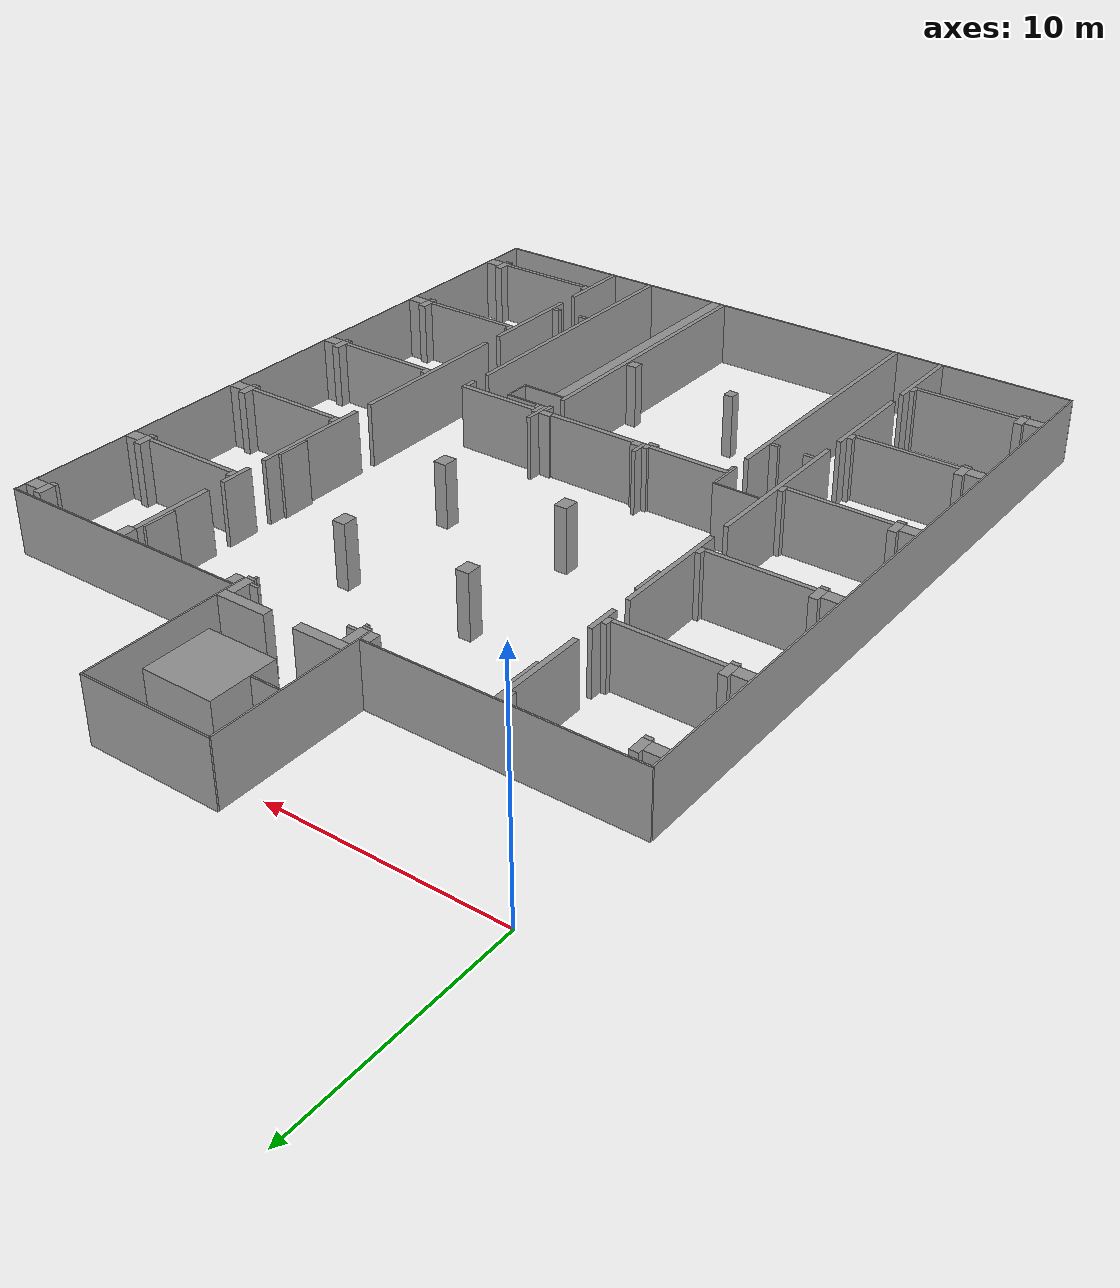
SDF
<?xml version="1.0" ?>
<sdf version="1.4">
  <model name="Bauman">
    <static>1</static>
    <link name="Wall_0">
      <collision name="Wall_0_Collision">
        <geometry>
          <box>
            <size>6.17750 0.07060 3.00000</size>
          </box>
        </geometry>
        <pose>15.37315 -0.03530 0 0 0 0.00000</pose>
      </collision>
      <visual name="Wall_0_Visual">
        <geometry>
          <box>
            <size>6.17750 0.07060 3.00000</size>
          </box>
        </geometry>
        <material>
          <script>
            <uri>file://media/materials/scripts/gazebo.material</uri>
            <name>Gazebo/Grey</name>
          </script>
        </material>
        <pose>15.37315 -0.03530 0 0 0 0.00000</pose>
      </visual>
    </link>
    <link name="Wall_1">
      <collision name="Wall_1_Collision">
        <geometry>
          <box>
            <size>0.07060 7.69540 3.00000</size>
          </box>
        </geometry>
        <pose>12.31970 -3.91830 0 0 0 0.00000</pose>
      </collision>
      <visual name="Wall_1_Visual">
        <geometry>
          <box>
            <size>0.07060 7.69540 3.00000</size>
          </box>
        </geometry>
        <material>
          <script>
            <uri>file://media/materials/scripts/gazebo.material</uri>
            <name>Gazebo/Grey</name>
          </script>
        </material>
        <pose>12.31970 -3.91830 0 0 0 0.00000</pose>
      </visual>
    </link>
    <link name="Wall_2">
      <collision name="Wall_2_Collision">
        <geometry>
          <box>
            <size>0.07060 7.69540 3.00000</size>
          </box>
        </geometry>
        <pose>18.42660 -3.91830 0 0 0 0.00000</pose>
      </collision>
      <visual name="Wall_2_Visual">
        <geometry>
          <box>
            <size>0.07060 7.69540 3.00000</size>
          </box>
        </geometry>
        <material>
          <script>
            <uri>file://media/materials/scripts/gazebo.material</uri>
            <name>Gazebo/Grey</name>
          </script>
        </material>
        <pose>18.42660 -3.91830 0 0 0 0.00000</pose>
      </visual>
    </link>
    <link name="Wall_3">
      <collision name="Wall_3_Collision">
        <geometry>
          <box>
            <size>3.24760 3.10640 3.00000</size>
          </box>
        </geometry>
        <pose>15.35550 -3.00050 0 0 0 0.00000</pose>
      </collision>
      <visual name="Wall_3_Visual">
        <geometry>
          <box>
            <size>3.24760 3.10640 3.00000</size>
          </box>
        </geometry>
        <material>
          <script>
            <uri>file://media/materials/scripts/gazebo.material</uri>
            <name>Gazebo/Grey</name>
          </script>
        </material>
        <pose>15.35550 -3.00050 0 0 0 0.00000</pose>
      </visual>
    </link>
    <link name="Wall_4">
      <collision name="Wall_4_Collision">
        <geometry>
          <box>
            <size>1.37670 0.07060 3.00000</size>
          </box>
        </geometry>
        <pose>13.04335 -3.31820 0 0 0 0.00000</pose>
      </collision>
      <visual name="Wall_4_Visual">
        <geometry>
          <box>
            <size>1.37670 0.07060 3.00000</size>
          </box>
        </geometry>
        <material>
          <script>
            <uri>file://media/materials/scripts/gazebo.material</uri>
            <name>Gazebo/Grey</name>
          </script>
        </material>
        <pose>13.04335 -3.31820 0 0 0 0.00000</pose>
      </visual>
    </link>
    <link name="Wall_5">
      <collision name="Wall_5_Collision">
        <geometry>
          <box>
            <size>2.29450 0.45890 3.00000</size>
          </box>
        </geometry>
        <pose>13.50225 -6.51285 0 0 0 0.00000</pose>
      </collision>
      <visual name="Wall_5_Visual">
        <geometry>
          <box>
            <size>2.29450 0.45890 3.00000</size>
          </box>
        </geometry>
        <material>
          <script>
            <uri>file://media/materials/scripts/gazebo.material</uri>
            <name>Gazebo/Grey</name>
          </script>
        </material>
        <pose>13.50225 -6.51285 0 0 0 0.00000</pose>
      </visual>
    </link>
    <link name="Wall_6">
      <collision name="Wall_6_Collision">
        <geometry>
          <box>
            <size>2.32980 0.45890 3.00000</size>
          </box>
        </geometry>
        <pose>17.22640 -6.51285 0 0 0 0.00000</pose>
      </collision>
      <visual name="Wall_6_Visual">
        <geometry>
          <box>
            <size>2.32980 0.45890 3.00000</size>
          </box>
        </geometry>
        <material>
          <script>
            <uri>file://media/materials/scripts/gazebo.material</uri>
            <name>Gazebo/Grey</name>
          </script>
        </material>
        <pose>17.22640 -6.51285 0 0 0 0.00000</pose>
      </visual>
    </link>
    <link name="Wall_7">
      <collision name="Wall_7_Collision">
        <geometry>
          <box>
            <size>0.42360 1.02370 3.00000</size>
          </box>
        </geometry>
        <pose>12.56680 -7.25415 0 0 0 0.00000</pose>
      </collision>
      <visual name="Wall_7_Visual">
        <geometry>
          <box>
            <size>0.42360 1.02370 3.00000</size>
          </box>
        </geometry>
        <material>
          <script>
            <uri>file://media/materials/scripts/gazebo.material</uri>
            <name>Gazebo/Grey</name>
          </script>
        </material>
        <pose>12.56680 -7.25415 0 0 0 0.00000</pose>
      </visual>
    </link>
    <link name="Wall_8">
      <collision name="Wall_8_Collision">
        <geometry>
          <box>
            <size>0.42360 1.02370 3.00000</size>
          </box>
        </geometry>
        <pose>18.17950 -7.25415 0 0 0 0.00000</pose>
      </collision>
      <visual name="Wall_8_Visual">
        <geometry>
          <box>
            <size>0.42360 1.02370 3.00000</size>
          </box>
        </geometry>
        <material>
          <script>
            <uri>file://media/materials/scripts/gazebo.material</uri>
            <name>Gazebo/Grey</name>
          </script>
        </material>
        <pose>18.17950 -7.25415 0 0 0 0.00000</pose>
      </visual>
    </link>
    <link name="Wall_9">
      <collision name="Wall_9_Collision">
        <geometry>
          <box>
            <size>12.28440 0.07060 3.00000</size>
          </box>
        </geometry>
        <pose>6.14220 -7.16590 0 0 0 0.00000</pose>
      </collision>
      <visual name="Wall_9_Visual">
        <geometry>
          <box>
            <size>12.28440 0.07060 3.00000</size>
          </box>
        </geometry>
        <material>
          <script>
            <uri>file://media/materials/scripts/gazebo.material</uri>
            <name>Gazebo/Grey</name>
          </script>
        </material>
        <pose>6.14220 -7.16590 0 0 0 0.00000</pose>
      </visual>
    </link>
    <link name="Wall_10">
      <collision name="Wall_10_Collision">
        <geometry>
          <box>
            <size>12.21380 0.07060 3.00000</size>
          </box>
        </geometry>
        <pose>24.56880 -7.16590 0 0 0 0.00000</pose>
      </collision>
      <visual name="Wall_10_Visual">
        <geometry>
          <box>
            <size>12.21380 0.07060 3.00000</size>
          </box>
        </geometry>
        <material>
          <script>
            <uri>file://media/materials/scripts/gazebo.material</uri>
            <name>Gazebo/Grey</name>
          </script>
        </material>
        <pose>24.56880 -7.16590 0 0 0 0.00000</pose>
      </visual>
    </link>
    <link name="Wall_11">
      <collision name="Wall_11_Collision">
        <geometry>
          <box>
            <size>0.07060 32.51130 3.00000</size>
          </box>
        </geometry>
        <pose>0.03530 -23.45685 0 0 0 0.00000</pose>
      </collision>
      <visual name="Wall_11_Visual">
        <geometry>
          <box>
            <size>0.07060 32.51130 3.00000</size>
          </box>
        </geometry>
        <material>
          <script>
            <uri>file://media/materials/scripts/gazebo.material</uri>
            <name>Gazebo/Grey</name>
          </script>
        </material>
        <pose>0.03530 -23.45685 0 0 0 0.00000</pose>
      </visual>
    </link>
    <link name="Wall_12">
      <collision name="Wall_12_Collision">
        <geometry>
          <box>
            <size>0.45890 0.63540 3.00000</size>
          </box>
        </geometry>
        <pose>6.15985 -7.51890 0 0 0 0.00000</pose>
      </collision>
      <visual name="Wall_12_Visual">
        <geometry>
          <box>
            <size>0.45890 0.63540 3.00000</size>
          </box>
        </geometry>
        <material>
          <script>
            <uri>file://media/materials/scripts/gazebo.material</uri>
            <name>Gazebo/Grey</name>
          </script>
        </material>
        <pose>6.15985 -7.51890 0 0 0 0.00000</pose>
      </visual>
    </link>
    <link name="Wall_13">
      <collision name="Wall_13_Collision">
        <geometry>
          <box>
            <size>0.42360 0.56480 3.00000</size>
          </box>
        </geometry>
        <pose>12.07260 -7.48360 0 0 0 0.00000</pose>
      </collision>
      <visual name="Wall_13_Visual">
        <geometry>
          <box>
            <size>0.42360 0.56480 3.00000</size>
          </box>
        </geometry>
        <material>
          <script>
            <uri>file://media/materials/scripts/gazebo.material</uri>
            <name>Gazebo/Grey</name>
          </script>
        </material>
        <pose>12.07260 -7.48360 0 0 0 0.00000</pose>
      </visual>
    </link>
    <link name="Wall_14">
      <collision name="Wall_14_Collision">
        <geometry>
          <box>
            <size>0.42360 0.56480 3.00000</size>
          </box>
        </geometry>
        <pose>18.67370 -7.48360 0 0 0 0.00000</pose>
      </collision>
      <visual name="Wall_14_Visual">
        <geometry>
          <box>
            <size>0.42360 0.56480 3.00000</size>
          </box>
        </geometry>
        <material>
          <script>
            <uri>file://media/materials/scripts/gazebo.material</uri>
            <name>Gazebo/Grey</name>
          </script>
        </material>
        <pose>18.67370 -7.48360 0 0 0 0.00000</pose>
      </visual>
    </link>
    <link name="Wall_15">
      <collision name="Wall_15_Collision">
        <geometry>
          <box>
            <size>0.45890 0.63540 3.00000</size>
          </box>
        </geometry>
        <pose>24.55115 -7.51890 0 0 0 0.00000</pose>
      </collision>
      <visual name="Wall_15_Visual">
        <geometry>
          <box>
            <size>0.45890 0.63540 3.00000</size>
          </box>
        </geometry>
        <material>
          <script>
            <uri>file://media/materials/scripts/gazebo.material</uri>
            <name>Gazebo/Grey</name>
          </script>
        </material>
        <pose>24.55115 -7.51890 0 0 0 0.00000</pose>
      </visual>
    </link>
    <link name="Wall_16">
      <collision name="Wall_16_Collision">
        <geometry>
          <box>
            <size>0.03530 32.51130 3.00000</size>
          </box>
        </geometry>
        <pose>30.65805 -23.45685 0 0 0 0.00000</pose>
      </collision>
      <visual name="Wall_16_Visual">
        <geometry>
          <box>
            <size>0.03530 32.51130 3.00000</size>
          </box>
        </geometry>
        <material>
          <script>
            <uri>file://media/materials/scripts/gazebo.material</uri>
            <name>Gazebo/Grey</name>
          </script>
        </material>
        <pose>30.65805 -23.45685 0 0 0 0.00000</pose>
      </visual>
    </link>
    <link name="Wall_17">
      <collision name="Wall_17_Collision">
        <geometry>
          <box>
            <size>0.38830 0.77660 3.00000</size>
          </box>
        </geometry>
        <pose>0.97075 -7.87190 0 0 0 0.00000</pose>
      </collision>
      <visual name="Wall_17_Visual">
        <geometry>
          <box>
            <size>0.38830 0.77660 3.00000</size>
          </box>
        </geometry>
        <material>
          <script>
            <uri>file://media/materials/scripts/gazebo.material</uri>
            <name>Gazebo/Grey</name>
          </script>
        </material>
        <pose>0.97075 -7.87190 0 0 0 0.00000</pose>
      </visual>
    </link>
    <link name="Wall_18">
      <collision name="Wall_18_Collision">
        <geometry>
          <box>
            <size>0.42360 0.14120 3.00000</size>
          </box>
        </geometry>
        <pose>12.99040 -7.55420 0 0 0 0.00000</pose>
      </collision>
      <visual name="Wall_18_Visual">
        <geometry>
          <box>
            <size>0.42360 0.14120 3.00000</size>
          </box>
        </geometry>
        <material>
          <script>
            <uri>file://media/materials/scripts/gazebo.material</uri>
            <name>Gazebo/Grey</name>
          </script>
        </material>
        <pose>12.99040 -7.55420 0 0 0 0.00000</pose>
      </visual>
    </link>
    <link name="Wall_19">
      <collision name="Wall_19_Collision">
        <geometry>
          <box>
            <size>0.42360 0.14120 3.00000</size>
          </box>
        </geometry>
        <pose>17.75590 -7.55420 0 0 0 0.00000</pose>
      </collision>
      <visual name="Wall_19_Visual">
        <geometry>
          <box>
            <size>0.42360 0.14120 3.00000</size>
          </box>
        </geometry>
        <material>
          <script>
            <uri>file://media/materials/scripts/gazebo.material</uri>
            <name>Gazebo/Grey</name>
          </script>
        </material>
        <pose>17.75590 -7.55420 0 0 0 0.00000</pose>
      </visual>
    </link>
    <link name="Wall_20">
      <collision name="Wall_20_Collision">
        <geometry>
          <box>
            <size>0.38830 0.77660 3.00000</size>
          </box>
        </geometry>
        <pose>29.74025 -7.87190 0 0 0 0.00000</pose>
      </collision>
      <visual name="Wall_20_Visual">
        <geometry>
          <box>
            <size>0.38830 0.77660 3.00000</size>
          </box>
        </geometry>
        <material>
          <script>
            <uri>file://media/materials/scripts/gazebo.material</uri>
            <name>Gazebo/Grey</name>
          </script>
        </material>
        <pose>29.74025 -7.87190 0 0 0 0.00000</pose>
      </visual>
    </link>
    <link name="Wall_21">
      <collision name="Wall_21_Collision">
        <geometry>
          <box>
            <size>0.70600 0.56480 3.00000</size>
          </box>
        </geometry>
        <pose>0.42360 -7.97780 0 0 0 0.00000</pose>
      </collision>
      <visual name="Wall_21_Visual">
        <geometry>
          <box>
            <size>0.70600 0.56480 3.00000</size>
          </box>
        </geometry>
        <material>
          <script>
            <uri>file://media/materials/scripts/gazebo.material</uri>
            <name>Gazebo/Grey</name>
          </script>
        </material>
        <pose>0.42360 -7.97780 0 0 0 0.00000</pose>
      </visual>
    </link>
    <link name="Wall_22">
      <collision name="Wall_22_Collision">
        <geometry>
          <box>
            <size>0.70600 0.56480 3.00000</size>
          </box>
        </geometry>
        <pose>30.28740 -7.97780 0 0 0 0.00000</pose>
      </collision>
      <visual name="Wall_22_Visual">
        <geometry>
          <box>
            <size>0.70600 0.56480 3.00000</size>
          </box>
        </geometry>
        <material>
          <script>
            <uri>file://media/materials/scripts/gazebo.material</uri>
            <name>Gazebo/Grey</name>
          </script>
        </material>
        <pose>30.28740 -7.97780 0 0 0 0.00000</pose>
      </visual>
    </link>
    <link name="Wall_23">
      <collision name="Wall_23_Collision">
        <geometry>
          <box>
            <size>0.38830 0.14120 3.00000</size>
          </box>
        </geometry>
        <pose>12.54915 -7.83660 0 0 0 0.00000</pose>
      </collision>
      <visual name="Wall_23_Visual">
        <geometry>
          <box>
            <size>0.38830 0.14120 3.00000</size>
          </box>
        </geometry>
        <material>
          <script>
            <uri>file://media/materials/scripts/gazebo.material</uri>
            <name>Gazebo/Grey</name>
          </script>
        </material>
        <pose>12.54915 -7.83660 0 0 0 0.00000</pose>
      </visual>
    </link>
    <link name="Wall_24">
      <collision name="Wall_24_Collision">
        <geometry>
          <box>
            <size>0.38830 0.14120 3.00000</size>
          </box>
        </geometry>
        <pose>18.19715 -7.83660 0 0 0 0.00000</pose>
      </collision>
      <visual name="Wall_24_Visual">
        <geometry>
          <box>
            <size>0.38830 0.14120 3.00000</size>
          </box>
        </geometry>
        <material>
          <script>
            <uri>file://media/materials/scripts/gazebo.material</uri>
            <name>Gazebo/Grey</name>
          </script>
        </material>
        <pose>18.19715 -7.83660 0 0 0 0.00000</pose>
      </visual>
    </link>
    <link name="Wall_25">
      <collision name="Wall_25_Collision">
        <geometry>
          <box>
            <size>0.24710 3.81240 3.00000</size>
          </box>
        </geometry>
        <pose>6.26575 -9.74280 0 0 0 0.00000</pose>
      </collision>
      <visual name="Wall_25_Visual">
        <geometry>
          <box>
            <size>0.24710 3.81240 3.00000</size>
          </box>
        </geometry>
        <material>
          <script>
            <uri>file://media/materials/scripts/gazebo.material</uri>
            <name>Gazebo/Grey</name>
          </script>
        </material>
        <pose>6.26575 -9.74280 0 0 0 0.00000</pose>
      </visual>
    </link>
    <link name="Wall_26">
      <collision name="Wall_26_Collision">
        <geometry>
          <box>
            <size>0.24710 3.81240 3.00000</size>
          </box>
        </geometry>
        <pose>24.44525 -9.74280 0 0 0 0.00000</pose>
      </collision>
      <visual name="Wall_26_Visual">
        <geometry>
          <box>
            <size>0.24710 3.81240 3.00000</size>
          </box>
        </geometry>
        <material>
          <script>
            <uri>file://media/materials/scripts/gazebo.material</uri>
            <name>Gazebo/Grey</name>
          </script>
        </material>
        <pose>24.44525 -9.74280 0 0 0 0.00000</pose>
      </visual>
    </link>
    <link name="Wall_27">
      <collision name="Wall_27_Collision">
        <geometry>
          <box>
            <size>0.14120 0.14120 3.00000</size>
          </box>
        </geometry>
        <pose>12.67270 -7.97780 0 0 0 0.00000</pose>
      </collision>
      <visual name="Wall_27_Visual">
        <geometry>
          <box>
            <size>0.14120 0.14120 3.00000</size>
          </box>
        </geometry>
        <material>
          <script>
            <uri>file://media/materials/scripts/gazebo.material</uri>
            <name>Gazebo/Grey</name>
          </script>
        </material>
        <pose>12.67270 -7.97780 0 0 0 0.00000</pose>
      </visual>
    </link>
    <link name="Wall_28">
      <collision name="Wall_28_Collision">
        <geometry>
          <box>
            <size>0.14120 0.14120 3.00000</size>
          </box>
        </geometry>
        <pose>18.07360 -7.97780 0 0 0 0.00000</pose>
      </collision>
      <visual name="Wall_28_Visual">
        <geometry>
          <box>
            <size>0.14120 0.14120 3.00000</size>
          </box>
        </geometry>
        <material>
          <script>
            <uri>file://media/materials/scripts/gazebo.material</uri>
            <name>Gazebo/Grey</name>
          </script>
        </material>
        <pose>18.07360 -7.97780 0 0 0 0.00000</pose>
      </visual>
    </link>
    <link name="Wall_29">
      <collision name="Wall_29_Collision">
        <geometry>
          <box>
            <size>0.14120 1.55320 3.00000</size>
          </box>
        </geometry>
        <pose>6.45990 -8.93090 0 0 0 0.00000</pose>
      </collision>
      <visual name="Wall_29_Visual">
        <geometry>
          <box>
            <size>0.14120 1.55320 3.00000</size>
          </box>
        </geometry>
        <material>
          <script>
            <uri>file://media/materials/scripts/gazebo.material</uri>
            <name>Gazebo/Grey</name>
          </script>
        </material>
        <pose>6.45990 -8.93090 0 0 0 0.00000</pose>
      </visual>
    </link>
    <link name="Wall_30">
      <collision name="Wall_30_Collision">
        <geometry>
          <box>
            <size>0.14120 1.55320 3.00000</size>
          </box>
        </geometry>
        <pose>24.25110 -8.93090 0 0 0 0.00000</pose>
      </collision>
      <visual name="Wall_30_Visual">
        <geometry>
          <box>
            <size>0.14120 1.55320 3.00000</size>
          </box>
        </geometry>
        <material>
          <script>
            <uri>file://media/materials/scripts/gazebo.material</uri>
            <name>Gazebo/Grey</name>
          </script>
        </material>
        <pose>24.25110 -8.93090 0 0 0 0.00000</pose>
      </visual>
    </link>
    <link name="Wall_31">
      <collision name="Wall_31_Collision">
        <geometry>
          <box>
            <size>0.35300 0.17650 3.00000</size>
          </box>
        </geometry>
        <pose>0.98840 -8.34845 0 0 0 0.00000</pose>
      </collision>
      <visual name="Wall_31_Visual">
        <geometry>
          <box>
            <size>0.35300 0.17650 3.00000</size>
          </box>
        </geometry>
        <material>
          <script>
            <uri>file://media/materials/scripts/gazebo.material</uri>
            <name>Gazebo/Grey</name>
          </script>
        </material>
        <pose>0.98840 -8.34845 0 0 0 0.00000</pose>
      </visual>
    </link>
    <link name="Wall_32">
      <collision name="Wall_32_Collision">
        <geometry>
          <box>
            <size>0.35300 0.17650 3.00000</size>
          </box>
        </geometry>
        <pose>29.72260 -8.34845 0 0 0 0.00000</pose>
      </collision>
      <visual name="Wall_32_Visual">
        <geometry>
          <box>
            <size>0.35300 0.17650 3.00000</size>
          </box>
        </geometry>
        <material>
          <script>
            <uri>file://media/materials/scripts/gazebo.material</uri>
            <name>Gazebo/Grey</name>
          </script>
        </material>
        <pose>29.72260 -8.34845 0 0 0 0.00000</pose>
      </visual>
    </link>
    <link name="Wall_33">
      <collision name="Wall_33_Collision">
        <geometry>
          <box>
            <size>0.21180 1.51790 3.00000</size>
          </box>
        </geometry>
        <pose>6.28340 -13.21985 0 0 0 0.00000</pose>
      </collision>
      <visual name="Wall_33_Visual">
        <geometry>
          <box>
            <size>0.21180 1.51790 3.00000</size>
          </box>
        </geometry>
        <material>
          <script>
            <uri>file://media/materials/scripts/gazebo.material</uri>
            <name>Gazebo/Grey</name>
          </script>
        </material>
        <pose>6.28340 -13.21985 0 0 0 0.00000</pose>
      </visual>
    </link>
    <link name="Wall_34">
      <collision name="Wall_34_Collision">
        <geometry>
          <box>
            <size>0.21180 1.51790 3.00000</size>
          </box>
        </geometry>
        <pose>24.42760 -13.21985 0 0 0 0.00000</pose>
      </collision>
      <visual name="Wall_34_Visual">
        <geometry>
          <box>
            <size>0.21180 1.51790 3.00000</size>
          </box>
        </geometry>
        <material>
          <script>
            <uri>file://media/materials/scripts/gazebo.material</uri>
            <name>Gazebo/Grey</name>
          </script>
        </material>
        <pose>24.42760 -13.21985 0 0 0 0.00000</pose>
      </visual>
    </link>
    <link name="Wall_35">
      <collision name="Wall_35_Collision">
        <geometry>
          <box>
            <size>0.38830 0.77660 3.00000</size>
          </box>
        </geometry>
        <pose>0.97075 -13.13160 0 0 0 0.00000</pose>
      </collision>
      <visual name="Wall_35_Visual">
        <geometry>
          <box>
            <size>0.38830 0.77660 3.00000</size>
          </box>
        </geometry>
        <material>
          <script>
            <uri>file://media/materials/scripts/gazebo.material</uri>
            <name>Gazebo/Grey</name>
          </script>
        </material>
        <pose>0.97075 -13.13160 0 0 0 0.00000</pose>
      </visual>
    </link>
    <link name="Wall_36">
      <collision name="Wall_36_Collision">
        <geometry>
          <box>
            <size>0.38830 0.77660 3.00000</size>
          </box>
        </geometry>
        <pose>29.74025 -13.13160 0 0 0 0.00000</pose>
      </collision>
      <visual name="Wall_36_Visual">
        <geometry>
          <box>
            <size>0.38830 0.77660 3.00000</size>
          </box>
        </geometry>
        <material>
          <script>
            <uri>file://media/materials/scripts/gazebo.material</uri>
            <name>Gazebo/Grey</name>
          </script>
        </material>
        <pose>29.74025 -13.13160 0 0 0 0.00000</pose>
      </visual>
    </link>
    <link name="Wall_37">
      <collision name="Wall_37_Collision">
        <geometry>
          <box>
            <size>0.60010 0.70600 3.00000</size>
          </box>
        </geometry>
        <pose>12.30205 -13.13160 0 0 0 0.00000</pose>
      </collision>
      <visual name="Wall_37_Visual">
        <geometry>
          <box>
            <size>0.60010 0.70600 3.00000</size>
          </box>
        </geometry>
        <material>
          <script>
            <uri>file://media/materials/scripts/gazebo.material</uri>
            <name>Gazebo/Grey</name>
          </script>
        </material>
        <pose>12.30205 -13.13160 0 0 0 0.00000</pose>
      </visual>
    </link>
    <link name="Wall_38">
      <collision name="Wall_38_Collision">
        <geometry>
          <box>
            <size>0.60010 0.70600 3.00000</size>
          </box>
        </geometry>
        <pose>18.44425 -13.13160 0 0 0 0.00000</pose>
      </collision>
      <visual name="Wall_38_Visual">
        <geometry>
          <box>
            <size>0.60010 0.70600 3.00000</size>
          </box>
        </geometry>
        <material>
          <script>
            <uri>file://media/materials/scripts/gazebo.material</uri>
            <name>Gazebo/Grey</name>
          </script>
        </material>
        <pose>18.44425 -13.13160 0 0 0 0.00000</pose>
      </visual>
    </link>
    <link name="Wall_39">
      <collision name="Wall_39_Collision">
        <geometry>
          <box>
            <size>0.70600 0.56480 3.00000</size>
          </box>
        </geometry>
        <pose>0.42360 -13.23750 0 0 0 0.00000</pose>
      </collision>
      <visual name="Wall_39_Visual">
        <geometry>
          <box>
            <size>0.70600 0.56480 3.00000</size>
          </box>
        </geometry>
        <material>
          <script>
            <uri>file://media/materials/scripts/gazebo.material</uri>
            <name>Gazebo/Grey</name>
          </script>
        </material>
        <pose>0.42360 -13.23750 0 0 0 0.00000</pose>
      </visual>
    </link>
    <link name="Wall_40">
      <collision name="Wall_40_Collision">
        <geometry>
          <box>
            <size>0.70600 0.56480 3.00000</size>
          </box>
        </geometry>
        <pose>30.28740 -13.23750 0 0 0 0.00000</pose>
      </collision>
      <visual name="Wall_40_Visual">
        <geometry>
          <box>
            <size>0.70600 0.56480 3.00000</size>
          </box>
        </geometry>
        <material>
          <script>
            <uri>file://media/materials/scripts/gazebo.material</uri>
            <name>Gazebo/Grey</name>
          </script>
        </material>
        <pose>30.28740 -13.23750 0 0 0 0.00000</pose>
      </visual>
    </link>
    <link name="Wall_41">
      <collision name="Wall_41_Collision">
        <geometry>
          <box>
            <size>0.24710 0.45890 3.00000</size>
          </box>
        </geometry>
        <pose>6.05395 -13.21985 0 0 0 0.00000</pose>
      </collision>
      <visual name="Wall_41_Visual">
        <geometry>
          <box>
            <size>0.24710 0.45890 3.00000</size>
          </box>
        </geometry>
        <material>
          <script>
            <uri>file://media/materials/scripts/gazebo.material</uri>
            <name>Gazebo/Grey</name>
          </script>
        </material>
        <pose>6.05395 -13.21985 0 0 0 0.00000</pose>
      </visual>
    </link>
    <link name="Wall_42">
      <collision name="Wall_42_Collision">
        <geometry>
          <box>
            <size>0.24710 0.45890 3.00000</size>
          </box>
        </geometry>
        <pose>24.65705 -13.21985 0 0 0 0.00000</pose>
      </collision>
      <visual name="Wall_42_Visual">
        <geometry>
          <box>
            <size>0.24710 0.45890 3.00000</size>
          </box>
        </geometry>
        <material>
          <script>
            <uri>file://media/materials/scripts/gazebo.material</uri>
            <name>Gazebo/Grey</name>
          </script>
        </material>
        <pose>24.65705 -13.21985 0 0 0 0.00000</pose>
      </visual>
    </link>
    <link name="Wall_43">
      <collision name="Wall_43_Collision">
        <geometry>
          <box>
            <size>4.76550 0.21180 3.00000</size>
          </box>
        </geometry>
        <pose>3.54765 -13.34340 0 0 0 0.00000</pose>
      </collision>
      <visual name="Wall_43_Visual">
        <geometry>
          <box>
            <size>4.76550 0.21180 3.00000</size>
          </box>
        </geometry>
        <material>
          <script>
            <uri>file://media/materials/scripts/gazebo.material</uri>
            <name>Gazebo/Grey</name>
          </script>
        </material>
        <pose>3.54765 -13.34340 0 0 0 0.00000</pose>
      </visual>
    </link>
    <link name="Wall_44">
      <collision name="Wall_44_Collision">
        <geometry>
          <box>
            <size>4.76550 0.21180 3.00000</size>
          </box>
        </geometry>
        <pose>27.16335 -13.34340 0 0 0 0.00000</pose>
      </collision>
      <visual name="Wall_44_Visual">
        <geometry>
          <box>
            <size>4.76550 0.21180 3.00000</size>
          </box>
        </geometry>
        <material>
          <script>
            <uri>file://media/materials/scripts/gazebo.material</uri>
            <name>Gazebo/Grey</name>
          </script>
        </material>
        <pose>27.16335 -13.34340 0 0 0 0.00000</pose>
      </visual>
    </link>
    <link name="Wall_45">
      <collision name="Wall_45_Collision">
        <geometry>
          <box>
            <size>0.35300 0.17650 3.00000</size>
          </box>
        </geometry>
        <pose>0.98840 -13.60815 0 0 0 0.00000</pose>
      </collision>
      <visual name="Wall_45_Visual">
        <geometry>
          <box>
            <size>0.35300 0.17650 3.00000</size>
          </box>
        </geometry>
        <material>
          <script>
            <uri>file://media/materials/scripts/gazebo.material</uri>
            <name>Gazebo/Grey</name>
          </script>
        </material>
        <pose>0.98840 -13.60815 0 0 0 0.00000</pose>
      </visual>
    </link>
    <link name="Wall_46">
      <collision name="Wall_46_Collision">
        <geometry>
          <box>
            <size>0.35300 0.17650 3.00000</size>
          </box>
        </geometry>
        <pose>29.72260 -13.60815 0 0 0 0.00000</pose>
      </collision>
      <visual name="Wall_46_Visual">
        <geometry>
          <box>
            <size>0.35300 0.17650 3.00000</size>
          </box>
        </geometry>
        <material>
          <script>
            <uri>file://media/materials/scripts/gazebo.material</uri>
            <name>Gazebo/Grey</name>
          </script>
        </material>
        <pose>29.72260 -13.60815 0 0 0 0.00000</pose>
      </visual>
    </link>
    <link name="Wall_47">
      <collision name="Wall_47_Collision">
        <geometry>
          <box>
            <size>0.21180 5.64800 3.00000</size>
          </box>
        </geometry>
        <pose>6.28340 -17.61470 0 0 0 0.00000</pose>
      </collision>
      <visual name="Wall_47_Visual">
        <geometry>
          <box>
            <size>0.21180 5.64800 3.00000</size>
          </box>
        </geometry>
        <material>
          <script>
            <uri>file://media/materials/scripts/gazebo.material</uri>
            <name>Gazebo/Grey</name>
          </script>
        </material>
        <pose>6.28340 -17.61470 0 0 0 0.00000</pose>
      </visual>
    </link>
    <link name="Wall_48">
      <collision name="Wall_48_Collision">
        <geometry>
          <box>
            <size>0.21180 5.64800 3.00000</size>
          </box>
        </geometry>
        <pose>24.42760 -17.61470 0 0 0 0.00000</pose>
      </collision>
      <visual name="Wall_48_Visual">
        <geometry>
          <box>
            <size>0.21180 5.64800 3.00000</size>
          </box>
        </geometry>
        <material>
          <script>
            <uri>file://media/materials/scripts/gazebo.material</uri>
            <name>Gazebo/Grey</name>
          </script>
        </material>
        <pose>24.42760 -17.61470 0 0 0 0.00000</pose>
      </visual>
    </link>
    <link name="Wall_49">
      <collision name="Wall_49_Collision">
        <geometry>
          <box>
            <size>0.14120 1.55320 3.00000</size>
          </box>
        </geometry>
        <pose>6.45990 -16.34390 0 0 0 0.00000</pose>
      </collision>
      <visual name="Wall_49_Visual">
        <geometry>
          <box>
            <size>0.14120 1.55320 3.00000</size>
          </box>
        </geometry>
        <material>
          <script>
            <uri>file://media/materials/scripts/gazebo.material</uri>
            <name>Gazebo/Grey</name>
          </script>
        </material>
        <pose>6.45990 -16.34390 0 0 0 0.00000</pose>
      </visual>
    </link>
    <link name="Wall_50">
      <collision name="Wall_50_Collision">
        <geometry>
          <box>
            <size>0.14120 1.55320 3.00000</size>
          </box>
        </geometry>
        <pose>24.25110 -16.34390 0 0 0 0.00000</pose>
      </collision>
      <visual name="Wall_50_Visual">
        <geometry>
          <box>
            <size>0.14120 1.55320 3.00000</size>
          </box>
        </geometry>
        <material>
          <script>
            <uri>file://media/materials/scripts/gazebo.material</uri>
            <name>Gazebo/Grey</name>
          </script>
        </material>
        <pose>24.25110 -16.34390 0 0 0 0.00000</pose>
      </visual>
    </link>
    <link name="Wall_51">
      <collision name="Wall_51_Collision">
        <geometry>
          <box>
            <size>0.38830 0.77660 3.00000</size>
          </box>
        </geometry>
        <pose>0.97075 -19.20320 0 0 0 0.00000</pose>
      </collision>
      <visual name="Wall_51_Visual">
        <geometry>
          <box>
            <size>0.38830 0.77660 3.00000</size>
          </box>
        </geometry>
        <material>
          <script>
            <uri>file://media/materials/scripts/gazebo.material</uri>
            <name>Gazebo/Grey</name>
          </script>
        </material>
        <pose>0.97075 -19.20320 0 0 0 0.00000</pose>
      </visual>
    </link>
    <link name="Wall_52">
      <collision name="Wall_52_Collision">
        <geometry>
          <box>
            <size>0.38830 0.77660 3.00000</size>
          </box>
        </geometry>
        <pose>29.74025 -19.20320 0 0 0 0.00000</pose>
      </collision>
      <visual name="Wall_52_Visual">
        <geometry>
          <box>
            <size>0.38830 0.77660 3.00000</size>
          </box>
        </geometry>
        <material>
          <script>
            <uri>file://media/materials/scripts/gazebo.material</uri>
            <name>Gazebo/Grey</name>
          </script>
        </material>
        <pose>29.74025 -19.20320 0 0 0 0.00000</pose>
      </visual>
    </link>
    <link name="Wall_53">
      <collision name="Wall_53_Collision">
        <geometry>
          <box>
            <size>0.60010 0.70600 3.00000</size>
          </box>
        </geometry>
        <pose>12.30205 -19.20320 0 0 0 0.00000</pose>
      </collision>
      <visual name="Wall_53_Visual">
        <geometry>
          <box>
            <size>0.60010 0.70600 3.00000</size>
          </box>
        </geometry>
        <material>
          <script>
            <uri>file://media/materials/scripts/gazebo.material</uri>
            <name>Gazebo/Grey</name>
          </script>
        </material>
        <pose>12.30205 -19.20320 0 0 0 0.00000</pose>
      </visual>
    </link>
    <link name="Wall_54">
      <collision name="Wall_54_Collision">
        <geometry>
          <box>
            <size>0.60010 0.70600 3.00000</size>
          </box>
        </geometry>
        <pose>18.44425 -19.20320 0 0 0 0.00000</pose>
      </collision>
      <visual name="Wall_54_Visual">
        <geometry>
          <box>
            <size>0.60010 0.70600 3.00000</size>
          </box>
        </geometry>
        <material>
          <script>
            <uri>file://media/materials/scripts/gazebo.material</uri>
            <name>Gazebo/Grey</name>
          </script>
        </material>
        <pose>18.44425 -19.20320 0 0 0 0.00000</pose>
      </visual>
    </link>
    <link name="Wall_55">
      <collision name="Wall_55_Collision">
        <geometry>
          <box>
            <size>0.70600 0.56480 3.00000</size>
          </box>
        </geometry>
        <pose>0.42360 -19.30910 0 0 0 0.00000</pose>
      </collision>
      <visual name="Wall_55_Visual">
        <geometry>
          <box>
            <size>0.70600 0.56480 3.00000</size>
          </box>
        </geometry>
        <material>
          <script>
            <uri>file://media/materials/scripts/gazebo.material</uri>
            <name>Gazebo/Grey</name>
          </script>
        </material>
        <pose>0.42360 -19.30910 0 0 0 0.00000</pose>
      </visual>
    </link>
    <link name="Wall_56">
      <collision name="Wall_56_Collision">
        <geometry>
          <box>
            <size>0.70600 0.56480 3.00000</size>
          </box>
        </geometry>
        <pose>30.28740 -19.30910 0 0 0 0.00000</pose>
      </collision>
      <visual name="Wall_56_Visual">
        <geometry>
          <box>
            <size>0.70600 0.56480 3.00000</size>
          </box>
        </geometry>
        <material>
          <script>
            <uri>file://media/materials/scripts/gazebo.material</uri>
            <name>Gazebo/Grey</name>
          </script>
        </material>
        <pose>30.28740 -19.30910 0 0 0 0.00000</pose>
      </visual>
    </link>
    <link name="Wall_57">
      <collision name="Wall_57_Collision">
        <geometry>
          <box>
            <size>0.24710 0.45890 3.00000</size>
          </box>
        </geometry>
        <pose>6.05395 -19.29145 0 0 0 0.00000</pose>
      </collision>
      <visual name="Wall_57_Visual">
        <geometry>
          <box>
            <size>0.24710 0.45890 3.00000</size>
          </box>
        </geometry>
        <material>
          <script>
            <uri>file://media/materials/scripts/gazebo.material</uri>
            <name>Gazebo/Grey</name>
          </script>
        </material>
        <pose>6.05395 -19.29145 0 0 0 0.00000</pose>
      </visual>
    </link>
    <link name="Wall_58">
      <collision name="Wall_58_Collision">
        <geometry>
          <box>
            <size>0.24710 0.45890 3.00000</size>
          </box>
        </geometry>
        <pose>24.65705 -19.29145 0 0 0 0.00000</pose>
      </collision>
      <visual name="Wall_58_Visual">
        <geometry>
          <box>
            <size>0.24710 0.45890 3.00000</size>
          </box>
        </geometry>
        <material>
          <script>
            <uri>file://media/materials/scripts/gazebo.material</uri>
            <name>Gazebo/Grey</name>
          </script>
        </material>
        <pose>24.65705 -19.29145 0 0 0 0.00000</pose>
      </visual>
    </link>
    <link name="Wall_59">
      <collision name="Wall_59_Collision">
        <geometry>
          <box>
            <size>4.76550 0.21180 3.00000</size>
          </box>
        </geometry>
        <pose>3.54765 -19.41500 0 0 0 0.00000</pose>
      </collision>
      <visual name="Wall_59_Visual">
        <geometry>
          <box>
            <size>4.76550 0.21180 3.00000</size>
          </box>
        </geometry>
        <material>
          <script>
            <uri>file://media/materials/scripts/gazebo.material</uri>
            <name>Gazebo/Grey</name>
          </script>
        </material>
        <pose>3.54765 -19.41500 0 0 0 0.00000</pose>
      </visual>
    </link>
    <link name="Wall_60">
      <collision name="Wall_60_Collision">
        <geometry>
          <box>
            <size>4.76550 0.21180 3.00000</size>
          </box>
        </geometry>
        <pose>27.16335 -19.41500 0 0 0 0.00000</pose>
      </collision>
      <visual name="Wall_60_Visual">
        <geometry>
          <box>
            <size>4.76550 0.21180 3.00000</size>
          </box>
        </geometry>
        <material>
          <script>
            <uri>file://media/materials/scripts/gazebo.material</uri>
            <name>Gazebo/Grey</name>
          </script>
        </material>
        <pose>27.16335 -19.41500 0 0 0 0.00000</pose>
      </visual>
    </link>
    <link name="Wall_61">
      <collision name="Wall_61_Collision">
        <geometry>
          <box>
            <size>0.35300 0.17650 3.00000</size>
          </box>
        </geometry>
        <pose>0.98840 -19.67975 0 0 0 0.00000</pose>
      </collision>
      <visual name="Wall_61_Visual">
        <geometry>
          <box>
            <size>0.35300 0.17650 3.00000</size>
          </box>
        </geometry>
        <material>
          <script>
            <uri>file://media/materials/scripts/gazebo.material</uri>
            <name>Gazebo/Grey</name>
          </script>
        </material>
        <pose>0.98840 -19.67975 0 0 0 0.00000</pose>
      </visual>
    </link>
    <link name="Wall_62">
      <collision name="Wall_62_Collision">
        <geometry>
          <box>
            <size>0.35300 0.17650 3.00000</size>
          </box>
        </geometry>
        <pose>29.72260 -19.67975 0 0 0 0.00000</pose>
      </collision>
      <visual name="Wall_62_Visual">
        <geometry>
          <box>
            <size>0.35300 0.17650 3.00000</size>
          </box>
        </geometry>
        <material>
          <script>
            <uri>file://media/materials/scripts/gazebo.material</uri>
            <name>Gazebo/Grey</name>
          </script>
        </material>
        <pose>29.72260 -19.67975 0 0 0 0.00000</pose>
      </visual>
    </link>
    <link name="Wall_63">
      <collision name="Wall_63_Collision">
        <geometry>
          <box>
            <size>0.21180 8.15430 3.00000</size>
          </box>
        </geometry>
        <pose>24.42760 -25.32775 0 0 0 0.00000</pose>
      </collision>
      <visual name="Wall_63_Visual">
        <geometry>
          <box>
            <size>0.21180 8.15430 3.00000</size>
          </box>
        </geometry>
        <material>
          <script>
            <uri>file://media/materials/scripts/gazebo.material</uri>
            <name>Gazebo/Grey</name>
          </script>
        </material>
        <pose>24.42760 -25.32775 0 0 0 0.00000</pose>
      </visual>
    </link>
    <link name="Wall_64">
      <collision name="Wall_64_Collision">
        <geometry>
          <box>
            <size>0.21180 7.97780 3.00000</size>
          </box>
        </geometry>
        <pose>6.28340 -25.38070 0 0 0 0.00000</pose>
      </collision>
      <visual name="Wall_64_Visual">
        <geometry>
          <box>
            <size>0.21180 7.97780 3.00000</size>
          </box>
        </geometry>
        <material>
          <script>
            <uri>file://media/materials/scripts/gazebo.material</uri>
            <name>Gazebo/Grey</name>
          </script>
        </material>
        <pose>6.28340 -25.38070 0 0 0 0.00000</pose>
      </visual>
    </link>
    <link name="Wall_65">
      <collision name="Wall_65_Collision">
        <geometry>
          <box>
            <size>2.18860 0.07060 3.00000</size>
          </box>
        </geometry>
        <pose>7.48360 -24.07460 0 0 0 0.00000</pose>
      </collision>
      <visual name="Wall_65_Visual">
        <geometry>
          <box>
            <size>2.18860 0.07060 3.00000</size>
          </box>
        </geometry>
        <material>
          <script>
            <uri>file://media/materials/scripts/gazebo.material</uri>
            <name>Gazebo/Grey</name>
          </script>
        </material>
        <pose>7.48360 -24.07460 0 0 0 0.00000</pose>
      </visual>
    </link>
    <link name="Wall_66">
      <collision name="Wall_66_Collision">
        <geometry>
          <box>
            <size>0.10590 1.65910 3.00000</size>
          </box>
        </geometry>
        <pose>8.52495 -24.93945 0 0 0 0.00000</pose>
      </collision>
      <visual name="Wall_66_Visual">
        <geometry>
          <box>
            <size>0.10590 1.65910 3.00000</size>
          </box>
        </geometry>
        <material>
          <script>
            <uri>file://media/materials/scripts/gazebo.material</uri>
            <name>Gazebo/Grey</name>
          </script>
        </material>
        <pose>8.52495 -24.93945 0 0 0 0.00000</pose>
      </visual>
    </link>
    <link name="Wall_67">
      <collision name="Wall_67_Collision">
        <geometry>
          <box>
            <size>0.17650 1.30610 3.00000</size>
          </box>
        </geometry>
        <pose>18.09125 -25.01005 0 0 0 0.00000</pose>
      </collision>
      <visual name="Wall_67_Visual">
        <geometry>
          <box>
            <size>0.17650 1.30610 3.00000</size>
          </box>
        </geometry>
        <material>
          <script>
            <uri>file://media/materials/scripts/gazebo.material</uri>
            <name>Gazebo/Grey</name>
          </script>
        </material>
        <pose>18.09125 -25.01005 0 0 0 0.00000</pose>
      </visual>
    </link>
    <link name="Wall_68">
      <collision name="Wall_68_Collision">
        <geometry>
          <box>
            <size>0.17650 0.88250 3.00000</size>
          </box>
        </geometry>
        <pose>12.69035 -24.86885 0 0 0 0.00000</pose>
      </collision>
      <visual name="Wall_68_Visual">
        <geometry>
          <box>
            <size>0.17650 0.88250 3.00000</size>
          </box>
        </geometry>
        <material>
          <script>
            <uri>file://media/materials/scripts/gazebo.material</uri>
            <name>Gazebo/Grey</name>
          </script>
        </material>
        <pose>12.69035 -24.86885 0 0 0 0.00000</pose>
      </visual>
    </link>
    <link name="Wall_69">
      <collision name="Wall_69_Collision">
        <geometry>
          <box>
            <size>0.38830 0.77660 3.00000</size>
          </box>
        </geometry>
        <pose>0.97075 -25.20420 0 0 0 0.00000</pose>
      </collision>
      <visual name="Wall_69_Visual">
        <geometry>
          <box>
            <size>0.38830 0.77660 3.00000</size>
          </box>
        </geometry>
        <material>
          <script>
            <uri>file://media/materials/scripts/gazebo.material</uri>
            <name>Gazebo/Grey</name>
          </script>
        </material>
        <pose>0.97075 -25.20420 0 0 0 0.00000</pose>
      </visual>
    </link>
    <link name="Wall_70">
      <collision name="Wall_70_Collision">
        <geometry>
          <box>
            <size>0.38830 0.77660 3.00000</size>
          </box>
        </geometry>
        <pose>29.74025 -25.27480 0 0 0 0.00000</pose>
      </collision>
      <visual name="Wall_70_Visual">
        <geometry>
          <box>
            <size>0.38830 0.77660 3.00000</size>
          </box>
        </geometry>
        <material>
          <script>
            <uri>file://media/materials/scripts/gazebo.material</uri>
            <name>Gazebo/Grey</name>
          </script>
        </material>
        <pose>29.74025 -25.27480 0 0 0 0.00000</pose>
      </visual>
    </link>
    <link name="Wall_71">
      <collision name="Wall_71_Collision">
        <geometry>
          <box>
            <size>0.24710 0.38830 3.00000</size>
          </box>
        </geometry>
        <pose>12.47855 -25.11595 0 0 0 0.00000</pose>
      </collision>
      <visual name="Wall_71_Visual">
        <geometry>
          <box>
            <size>0.24710 0.38830 3.00000</size>
          </box>
        </geometry>
        <material>
          <script>
            <uri>file://media/materials/scripts/gazebo.material</uri>
            <name>Gazebo/Grey</name>
          </script>
        </material>
        <pose>12.47855 -25.11595 0 0 0 0.00000</pose>
      </visual>
    </link>
    <link name="Wall_72">
      <collision name="Wall_72_Collision">
        <geometry>
          <box>
            <size>0.42360 0.38830 3.00000</size>
          </box>
        </geometry>
        <pose>12.99040 -25.11595 0 0 0 0.00000</pose>
      </collision>
      <visual name="Wall_72_Visual">
        <geometry>
          <box>
            <size>0.42360 0.38830 3.00000</size>
          </box>
        </geometry>
        <material>
          <script>
            <uri>file://media/materials/scripts/gazebo.material</uri>
            <name>Gazebo/Grey</name>
          </script>
        </material>
        <pose>12.99040 -25.11595 0 0 0 0.00000</pose>
      </visual>
    </link>
    <link name="Wall_73">
      <collision name="Wall_73_Collision">
        <geometry>
          <box>
            <size>0.21180 0.74130 3.00000</size>
          </box>
        </geometry>
        <pose>18.28540 -25.29245 0 0 0 0.00000</pose>
      </collision>
      <visual name="Wall_73_Visual">
        <geometry>
          <box>
            <size>0.21180 0.74130 3.00000</size>
          </box>
        </geometry>
        <material>
          <script>
            <uri>file://media/materials/scripts/gazebo.material</uri>
            <name>Gazebo/Grey</name>
          </script>
        </material>
        <pose>18.28540 -25.29245 0 0 0 0.00000</pose>
      </visual>
    </link>
    <link name="Wall_74">
      <collision name="Wall_74_Collision">
        <geometry>
          <box>
            <size>0.56480 0.35300 3.00000</size>
          </box>
        </geometry>
        <pose>17.72060 -25.13360 0 0 0 0.00000</pose>
      </collision>
      <visual name="Wall_74_Visual">
        <geometry>
          <box>
            <size>0.56480 0.35300 3.00000</size>
          </box>
        </geometry>
        <material>
          <script>
            <uri>file://media/materials/scripts/gazebo.material</uri>
            <name>Gazebo/Grey</name>
          </script>
        </material>
        <pose>17.72060 -25.13360 0 0 0 0.00000</pose>
      </visual>
    </link>
    <link name="Wall_75">
      <collision name="Wall_75_Collision">
        <geometry>
          <box>
            <size>0.70600 0.56480 3.00000</size>
          </box>
        </geometry>
        <pose>0.42360 -25.31010 0 0 0 0.00000</pose>
      </collision>
      <visual name="Wall_75_Visual">
        <geometry>
          <box>
            <size>0.70600 0.56480 3.00000</size>
          </box>
        </geometry>
        <material>
          <script>
            <uri>file://media/materials/scripts/gazebo.material</uri>
            <name>Gazebo/Grey</name>
          </script>
        </material>
        <pose>0.42360 -25.31010 0 0 0 0.00000</pose>
      </visual>
    </link>
    <link name="Wall_76">
      <collision name="Wall_76_Collision">
        <geometry>
          <box>
            <size>0.24710 0.45890 3.00000</size>
          </box>
        </geometry>
        <pose>6.05395 -25.29245 0 0 0 0.00000</pose>
      </collision>
      <visual name="Wall_76_Visual">
        <geometry>
          <box>
            <size>0.24710 0.45890 3.00000</size>
          </box>
        </geometry>
        <material>
          <script>
            <uri>file://media/materials/scripts/gazebo.material</uri>
            <name>Gazebo/Grey</name>
          </script>
        </material>
        <pose>6.05395 -25.29245 0 0 0 0.00000</pose>
      </visual>
    </link>
    <link name="Wall_77">
      <collision name="Wall_77_Collision">
        <geometry>
          <box>
            <size>3.77710 0.24710 3.00000</size>
          </box>
        </geometry>
        <pose>10.46645 -25.18655 0 0 0 0.00000</pose>
      </collision>
      <visual name="Wall_77_Visual">
        <geometry>
          <box>
            <size>3.77710 0.24710 3.00000</size>
          </box>
        </geometry>
        <material>
          <script>
            <uri>file://media/materials/scripts/gazebo.material</uri>
            <name>Gazebo/Grey</name>
          </script>
        </material>
        <pose>10.46645 -25.18655 0 0 0 0.00000</pose>
      </visual>
    </link>
    <link name="Wall_78">
      <collision name="Wall_78_Collision">
        <geometry>
          <box>
            <size>4.23600 0.24710 3.00000</size>
          </box>
        </geometry>
        <pose>15.32020 -25.18655 0 0 0 0.00000</pose>
      </collision>
      <visual name="Wall_78_Visual">
        <geometry>
          <box>
            <size>4.23600 0.24710 3.00000</size>
          </box>
        </geometry>
        <material>
          <script>
            <uri>file://media/materials/scripts/gazebo.material</uri>
            <name>Gazebo/Grey</name>
          </script>
        </material>
        <pose>15.32020 -25.18655 0 0 0 0.00000</pose>
      </visual>
    </link>
    <link name="Wall_79">
      <collision name="Wall_79_Collision">
        <geometry>
          <box>
            <size>3.95360 0.24710 3.00000</size>
          </box>
        </geometry>
        <pose>20.36810 -25.18655 0 0 0 0.00000</pose>
      </collision>
      <visual name="Wall_79_Visual">
        <geometry>
          <box>
            <size>3.95360 0.24710 3.00000</size>
          </box>
        </geometry>
        <material>
          <script>
            <uri>file://media/materials/scripts/gazebo.material</uri>
            <name>Gazebo/Grey</name>
          </script>
        </material>
        <pose>20.36810 -25.18655 0 0 0 0.00000</pose>
      </visual>
    </link>
    <link name="Wall_80">
      <collision name="Wall_80_Collision">
        <geometry>
          <box>
            <size>0.70600 0.56480 3.00000</size>
          </box>
        </geometry>
        <pose>30.28740 -25.38070 0 0 0 0.00000</pose>
      </collision>
      <visual name="Wall_80_Visual">
        <geometry>
          <box>
            <size>0.70600 0.56480 3.00000</size>
          </box>
        </geometry>
        <material>
          <script>
            <uri>file://media/materials/scripts/gazebo.material</uri>
            <name>Gazebo/Grey</name>
          </script>
        </material>
        <pose>30.28740 -25.38070 0 0 0 0.00000</pose>
      </visual>
    </link>
    <link name="Wall_81">
      <collision name="Wall_81_Collision">
        <geometry>
          <box>
            <size>0.28240 0.45890 3.00000</size>
          </box>
        </geometry>
        <pose>24.67470 -25.36305 0 0 0 0.00000</pose>
      </collision>
      <visual name="Wall_81_Visual">
        <geometry>
          <box>
            <size>0.28240 0.45890 3.00000</size>
          </box>
        </geometry>
        <material>
          <script>
            <uri>file://media/materials/scripts/gazebo.material</uri>
            <name>Gazebo/Grey</name>
          </script>
        </material>
        <pose>24.67470 -25.36305 0 0 0 0.00000</pose>
      </visual>
    </link>
    <link name="Wall_82">
      <collision name="Wall_82_Collision">
        <geometry>
          <box>
            <size>4.76550 0.21180 3.00000</size>
          </box>
        </geometry>
        <pose>3.54765 -25.41600 0 0 0 0.00000</pose>
      </collision>
      <visual name="Wall_82_Visual">
        <geometry>
          <box>
            <size>4.76550 0.21180 3.00000</size>
          </box>
        </geometry>
        <material>
          <script>
            <uri>file://media/materials/scripts/gazebo.material</uri>
            <name>Gazebo/Grey</name>
          </script>
        </material>
        <pose>3.54765 -25.41600 0 0 0 0.00000</pose>
      </visual>
    </link>
    <link name="Wall_83">
      <collision name="Wall_83_Collision">
        <geometry>
          <box>
            <size>0.10590 0.45890 3.00000</size>
          </box>
        </geometry>
        <pose>8.63085 -25.53955 0 0 0 0.00000</pose>
      </collision>
      <visual name="Wall_83_Visual">
        <geometry>
          <box>
            <size>0.10590 0.45890 3.00000</size>
          </box>
        </geometry>
        <material>
          <script>
            <uri>file://media/materials/scripts/gazebo.material</uri>
            <name>Gazebo/Grey</name>
          </script>
        </material>
        <pose>8.63085 -25.53955 0 0 0 0.00000</pose>
      </visual>
    </link>
    <link name="Wall_84">
      <collision name="Wall_84_Collision">
        <geometry>
          <box>
            <size>0.45890 0.21180 3.00000</size>
          </box>
        </geometry>
        <pose>12.33735 -25.41600 0 0 0 0.00000</pose>
      </collision>
      <visual name="Wall_84_Visual">
        <geometry>
          <box>
            <size>0.45890 0.21180 3.00000</size>
          </box>
        </geometry>
        <material>
          <script>
            <uri>file://media/materials/scripts/gazebo.material</uri>
            <name>Gazebo/Grey</name>
          </script>
        </material>
        <pose>12.33735 -25.41600 0 0 0 0.00000</pose>
      </visual>
    </link>
    <link name="Wall_85">
      <collision name="Wall_85_Collision">
        <geometry>
          <box>
            <size>0.17650 0.49420 3.00000</size>
          </box>
        </geometry>
        <pose>17.91475 -25.55720 0 0 0 0.00000</pose>
      </collision>
      <visual name="Wall_85_Visual">
        <geometry>
          <box>
            <size>0.17650 0.49420 3.00000</size>
          </box>
        </geometry>
        <material>
          <script>
            <uri>file://media/materials/scripts/gazebo.material</uri>
            <name>Gazebo/Grey</name>
          </script>
        </material>
        <pose>17.91475 -25.55720 0 0 0 0.00000</pose>
      </visual>
    </link>
    <link name="Wall_86">
      <collision name="Wall_86_Collision">
        <geometry>
          <box>
            <size>0.17650 0.35300 3.00000</size>
          </box>
        </geometry>
        <pose>18.47955 -25.48660 0 0 0 0.00000</pose>
      </collision>
      <visual name="Wall_86_Visual">
        <geometry>
          <box>
            <size>0.17650 0.35300 3.00000</size>
          </box>
        </geometry>
        <material>
          <script>
            <uri>file://media/materials/scripts/gazebo.material</uri>
            <name>Gazebo/Grey</name>
          </script>
        </material>
        <pose>18.47955 -25.48660 0 0 0 0.00000</pose>
      </visual>
    </link>
    <link name="Wall_87">
      <collision name="Wall_87_Collision">
        <geometry>
          <box>
            <size>0.21180 0.52950 3.00000</size>
          </box>
        </geometry>
        <pose>22.23900 -25.57485 0 0 0 0.00000</pose>
      </collision>
      <visual name="Wall_87_Visual">
        <geometry>
          <box>
            <size>0.21180 0.52950 3.00000</size>
          </box>
        </geometry>
        <material>
          <script>
            <uri>file://media/materials/scripts/gazebo.material</uri>
            <name>Gazebo/Grey</name>
          </script>
        </material>
        <pose>22.23900 -25.57485 0 0 0 0.00000</pose>
      </visual>
    </link>
    <link name="Wall_88">
      <collision name="Wall_88_Collision">
        <geometry>
          <box>
            <size>4.73020 0.21180 3.00000</size>
          </box>
        </geometry>
        <pose>27.18100 -25.48660 0 0 0 0.00000</pose>
      </collision>
      <visual name="Wall_88_Visual">
        <geometry>
          <box>
            <size>4.73020 0.21180 3.00000</size>
          </box>
        </geometry>
        <material>
          <script>
            <uri>file://media/materials/scripts/gazebo.material</uri>
            <name>Gazebo/Grey</name>
          </script>
        </material>
        <pose>27.18100 -25.48660 0 0 0 0.00000</pose>
      </visual>
    </link>
    <link name="Wall_89">
      <collision name="Wall_89_Collision">
        <geometry>
          <box>
            <size>0.35300 0.17650 3.00000</size>
          </box>
        </geometry>
        <pose>0.98840 -25.68075 0 0 0 0.00000</pose>
      </collision>
      <visual name="Wall_89_Visual">
        <geometry>
          <box>
            <size>0.35300 0.17650 3.00000</size>
          </box>
        </geometry>
        <material>
          <script>
            <uri>file://media/materials/scripts/gazebo.material</uri>
            <name>Gazebo/Grey</name>
          </script>
        </material>
        <pose>0.98840 -25.68075 0 0 0 0.00000</pose>
      </visual>
    </link>
    <link name="Wall_90">
      <collision name="Wall_90_Collision">
        <geometry>
          <box>
            <size>1.62380 0.07060 3.00000</size>
          </box>
        </geometry>
        <pose>19.37970 -25.62780 0 0 0 0.00000</pose>
      </collision>
      <visual name="Wall_90_Visual">
        <geometry>
          <box>
            <size>1.62380 0.07060 3.00000</size>
          </box>
        </geometry>
        <material>
          <script>
            <uri>file://media/materials/scripts/gazebo.material</uri>
            <name>Gazebo/Grey</name>
          </script>
        </material>
        <pose>19.37970 -25.62780 0 0 0 0.00000</pose>
      </visual>
    </link>
    <link name="Wall_91">
      <collision name="Wall_91_Collision">
        <geometry>
          <box>
            <size>0.03530 0.14120 3.00000</size>
          </box>
        </geometry>
        <pose>18.02065 -25.73370 0 0 0 0.00000</pose>
      </collision>
      <visual name="Wall_91_Visual">
        <geometry>
          <box>
            <size>0.03530 0.14120 3.00000</size>
          </box>
        </geometry>
        <material>
          <script>
            <uri>file://media/materials/scripts/gazebo.material</uri>
            <name>Gazebo/Grey</name>
          </script>
        </material>
        <pose>18.02065 -25.73370 0 0 0 0.00000</pose>
      </visual>
    </link>
    <link name="Wall_92">
      <collision name="Wall_92_Collision">
        <geometry>
          <box>
            <size>0.07060 1.20020 3.00000</size>
          </box>
        </geometry>
        <pose>20.15630 -26.26320 0 0 0 0.00000</pose>
      </collision>
      <visual name="Wall_92_Visual">
        <geometry>
          <box>
            <size>0.07060 1.20020 3.00000</size>
          </box>
        </geometry>
        <material>
          <script>
            <uri>file://media/materials/scripts/gazebo.material</uri>
            <name>Gazebo/Grey</name>
          </script>
        </material>
        <pose>20.15630 -26.26320 0 0 0 0.00000</pose>
      </visual>
    </link>
    <link name="Wall_93">
      <collision name="Wall_93_Collision">
        <geometry>
          <box>
            <size>0.35300 0.17650 3.00000</size>
          </box>
        </geometry>
        <pose>29.72260 -25.75135 0 0 0 0.00000</pose>
      </collision>
      <visual name="Wall_93_Visual">
        <geometry>
          <box>
            <size>0.35300 0.17650 3.00000</size>
          </box>
        </geometry>
        <material>
          <script>
            <uri>file://media/materials/scripts/gazebo.material</uri>
            <name>Gazebo/Grey</name>
          </script>
        </material>
        <pose>29.72260 -25.75135 0 0 0 0.00000</pose>
      </visual>
    </link>
    <link name="Wall_94">
      <collision name="Wall_94_Collision">
        <geometry>
          <box>
            <size>0.21180 13.13160 3.00000</size>
          </box>
        </geometry>
        <pose>17.93240 -33.14670 0 0 0 0.00000</pose>
      </collision>
      <visual name="Wall_94_Visual">
        <geometry>
          <box>
            <size>0.21180 13.13160 3.00000</size>
          </box>
        </geometry>
        <material>
          <script>
            <uri>file://media/materials/scripts/gazebo.material</uri>
            <name>Gazebo/Grey</name>
          </script>
        </material>
        <pose>17.93240 -33.14670 0 0 0 0.00000</pose>
      </visual>
    </link>
    <link name="Wall_95">
      <collision name="Wall_95_Collision">
        <geometry>
          <box>
            <size>0.21180 13.09630 3.00000</size>
          </box>
        </geometry>
        <pose>8.57790 -33.16435 0 0 0 0.00000</pose>
      </collision>
      <visual name="Wall_95_Visual">
        <geometry>
          <box>
            <size>0.21180 13.09630 3.00000</size>
          </box>
        </geometry>
        <material>
          <script>
            <uri>file://media/materials/scripts/gazebo.material</uri>
            <name>Gazebo/Grey</name>
          </script>
        </material>
        <pose>8.57790 -33.16435 0 0 0 0.00000</pose>
      </visual>
    </link>
    <link name="Wall_96">
      <collision name="Wall_96_Collision">
        <geometry>
          <box>
            <size>0.21180 13.06100 3.00000</size>
          </box>
        </geometry>
        <pose>22.20370 -33.18200 0 0 0 0.00000</pose>
      </collision>
      <visual name="Wall_96_Visual">
        <geometry>
          <box>
            <size>0.21180 13.06100 3.00000</size>
          </box>
        </geometry>
        <material>
          <script>
            <uri>file://media/materials/scripts/gazebo.material</uri>
            <name>Gazebo/Grey</name>
          </script>
        </material>
        <pose>22.20370 -33.18200 0 0 0 0.00000</pose>
      </visual>
    </link>
    <link name="Wall_97">
      <collision name="Wall_97_Collision">
        <geometry>
          <box>
            <size>2.08270 0.07060 3.00000</size>
          </box>
        </geometry>
        <pose>19.07965 -26.82800 0 0 0 0.00000</pose>
      </collision>
      <visual name="Wall_97_Visual">
        <geometry>
          <box>
            <size>2.08270 0.07060 3.00000</size>
          </box>
        </geometry>
        <material>
          <script>
            <uri>file://media/materials/scripts/gazebo.material</uri>
            <name>Gazebo/Grey</name>
          </script>
        </material>
        <pose>19.07965 -26.82800 0 0 0 0.00000</pose>
      </visual>
    </link>
    <link name="Wall_98">
      <collision name="Wall_98_Collision">
        <geometry>
          <box>
            <size>0.52950 12.84920 3.00000</size>
          </box>
        </geometry>
        <pose>18.30305 -33.28790 0 0 0 0.00000</pose>
      </collision>
      <visual name="Wall_98_Visual">
        <geometry>
          <box>
            <size>0.52950 12.84920 3.00000</size>
          </box>
        </geometry>
        <material>
          <script>
            <uri>file://media/materials/scripts/gazebo.material</uri>
            <name>Gazebo/Grey</name>
          </script>
        </material>
        <pose>18.30305 -33.28790 0 0 0 0.00000</pose>
      </visual>
    </link>
    <link name="Wall_99">
      <collision name="Wall_99_Collision">
        <geometry>
          <box>
            <size>0.49420 0.17650 3.00000</size>
          </box>
        </geometry>
        <pose>6.63640 -28.39885 0 0 0 0.00000</pose>
      </collision>
      <visual name="Wall_99_Visual">
        <geometry>
          <box>
            <size>0.49420 0.17650 3.00000</size>
          </box>
        </geometry>
        <material>
          <script>
            <uri>file://media/materials/scripts/gazebo.material</uri>
            <name>Gazebo/Grey</name>
          </script>
        </material>
        <pose>6.63640 -28.39885 0 0 0 0.00000</pose>
      </visual>
    </link>
    <link name="Wall_100">
      <collision name="Wall_100_Collision">
        <geometry>
          <box>
            <size>0.38830 0.17650 3.00000</size>
          </box>
        </geometry>
        <pose>8.27785 -28.39885 0 0 0 0.00000</pose>
      </collision>
      <visual name="Wall_100_Visual">
        <geometry>
          <box>
            <size>0.38830 0.17650 3.00000</size>
          </box>
        </geometry>
        <material>
          <script>
            <uri>file://media/materials/scripts/gazebo.material</uri>
            <name>Gazebo/Grey</name>
          </script>
        </material>
        <pose>8.27785 -28.39885 0 0 0 0.00000</pose>
      </visual>
    </link>
    <link name="Wall_101">
      <collision name="Wall_101_Collision">
        <geometry>
          <box>
            <size>0.21180 4.83610 3.00000</size>
          </box>
        </geometry>
        <pose>6.28340 -32.63485 0 0 0 0.00000</pose>
      </collision>
      <visual name="Wall_101_Visual">
        <geometry>
          <box>
            <size>0.21180 4.83610 3.00000</size>
          </box>
        </geometry>
        <material>
          <script>
            <uri>file://media/materials/scripts/gazebo.material</uri>
            <name>Gazebo/Grey</name>
          </script>
        </material>
        <pose>6.28340 -32.63485 0 0 0 0.00000</pose>
      </visual>
    </link>
    <link name="Wall_102">
      <collision name="Wall_102_Collision">
        <geometry>
          <box>
            <size>0.21180 5.01260 3.00000</size>
          </box>
        </geometry>
        <pose>24.42760 -32.79370 0 0 0 0.00000</pose>
      </collision>
      <visual name="Wall_102_Visual">
        <geometry>
          <box>
            <size>0.21180 5.01260 3.00000</size>
          </box>
        </geometry>
        <material>
          <script>
            <uri>file://media/materials/scripts/gazebo.material</uri>
            <name>Gazebo/Grey</name>
          </script>
        </material>
        <pose>24.42760 -32.79370 0 0 0 0.00000</pose>
      </visual>
    </link>
    <link name="Wall_103">
      <collision name="Wall_103_Collision">
        <geometry>
          <box>
            <size>0.38830 0.77660 3.00000</size>
          </box>
        </geometry>
        <pose>0.97075 -30.88750 0 0 0 0.00000</pose>
      </collision>
      <visual name="Wall_103_Visual">
        <geometry>
          <box>
            <size>0.38830 0.77660 3.00000</size>
          </box>
        </geometry>
        <material>
          <script>
            <uri>file://media/materials/scripts/gazebo.material</uri>
            <name>Gazebo/Grey</name>
          </script>
        </material>
        <pose>0.97075 -30.88750 0 0 0 0.00000</pose>
      </visual>
    </link>
    <link name="Wall_104">
      <collision name="Wall_104_Collision">
        <geometry>
          <box>
            <size>0.70600 0.56480 3.00000</size>
          </box>
        </geometry>
        <pose>0.42360 -30.99340 0 0 0 0.00000</pose>
      </collision>
      <visual name="Wall_104_Visual">
        <geometry>
          <box>
            <size>0.70600 0.56480 3.00000</size>
          </box>
        </geometry>
        <material>
          <script>
            <uri>file://media/materials/scripts/gazebo.material</uri>
            <name>Gazebo/Grey</name>
          </script>
        </material>
        <pose>0.42360 -30.99340 0 0 0 0.00000</pose>
      </visual>
    </link>
    <link name="Wall_105">
      <collision name="Wall_105_Collision">
        <geometry>
          <box>
            <size>0.24710 0.45890 3.00000</size>
          </box>
        </geometry>
        <pose>6.05395 -30.97575 0 0 0 0.00000</pose>
      </collision>
      <visual name="Wall_105_Visual">
        <geometry>
          <box>
            <size>0.24710 0.45890 3.00000</size>
          </box>
        </geometry>
        <material>
          <script>
            <uri>file://media/materials/scripts/gazebo.material</uri>
            <name>Gazebo/Grey</name>
          </script>
        </material>
        <pose>6.05395 -30.97575 0 0 0 0.00000</pose>
      </visual>
    </link>
    <link name="Wall_106">
      <collision name="Wall_106_Collision">
        <geometry>
          <box>
            <size>0.38830 0.70600 3.00000</size>
          </box>
        </geometry>
        <pose>29.66965 -31.31110 0 0 0 0.00000</pose>
      </collision>
      <visual name="Wall_106_Visual">
        <geometry>
          <box>
            <size>0.38830 0.70600 3.00000</size>
          </box>
        </geometry>
        <material>
          <script>
            <uri>file://media/materials/scripts/gazebo.material</uri>
            <name>Gazebo/Grey</name>
          </script>
        </material>
        <pose>29.66965 -31.31110 0 0 0 0.00000</pose>
      </visual>
    </link>
    <link name="Wall_107">
      <collision name="Wall_107_Collision">
        <geometry>
          <box>
            <size>4.76550 0.21180 3.00000</size>
          </box>
        </geometry>
        <pose>3.54765 -31.09930 0 0 0 0.00000</pose>
      </collision>
      <visual name="Wall_107_Visual">
        <geometry>
          <box>
            <size>4.76550 0.21180 3.00000</size>
          </box>
        </geometry>
        <material>
          <script>
            <uri>file://media/materials/scripts/gazebo.material</uri>
            <name>Gazebo/Grey</name>
          </script>
        </material>
        <pose>3.54765 -31.09930 0 0 0 0.00000</pose>
      </visual>
    </link>
    <link name="Wall_108">
      <collision name="Wall_108_Collision">
        <geometry>
          <box>
            <size>0.77660 0.56480 3.00000</size>
          </box>
        </geometry>
        <pose>30.25210 -31.45230 0 0 0 0.00000</pose>
      </collision>
      <visual name="Wall_108_Visual">
        <geometry>
          <box>
            <size>0.77660 0.56480 3.00000</size>
          </box>
        </geometry>
        <material>
          <script>
            <uri>file://media/materials/scripts/gazebo.material</uri>
            <name>Gazebo/Grey</name>
          </script>
        </material>
        <pose>30.25210 -31.45230 0 0 0 0.00000</pose>
      </visual>
    </link>
    <link name="Wall_109">
      <collision name="Wall_109_Collision">
        <geometry>
          <box>
            <size>0.21180 0.45890 3.00000</size>
          </box>
        </geometry>
        <pose>24.63940 -31.43465 0 0 0 0.00000</pose>
      </collision>
      <visual name="Wall_109_Visual">
        <geometry>
          <box>
            <size>0.21180 0.45890 3.00000</size>
          </box>
        </geometry>
        <material>
          <script>
            <uri>file://media/materials/scripts/gazebo.material</uri>
            <name>Gazebo/Grey</name>
          </script>
        </material>
        <pose>24.63940 -31.43465 0 0 0 0.00000</pose>
      </visual>
    </link>
    <link name="Wall_110">
      <collision name="Wall_110_Collision">
        <geometry>
          <box>
            <size>0.45890 0.49420 3.00000</size>
          </box>
        </geometry>
        <pose>12.33735 -31.48760 0 0 0 0.00000</pose>
      </collision>
      <visual name="Wall_110_Visual">
        <geometry>
          <box>
            <size>0.45890 0.49420 3.00000</size>
          </box>
        </geometry>
        <material>
          <script>
            <uri>file://media/materials/scripts/gazebo.material</uri>
            <name>Gazebo/Grey</name>
          </script>
        </material>
        <pose>12.33735 -31.48760 0 0 0 0.00000</pose>
      </visual>
    </link>
    <link name="Wall_111">
      <collision name="Wall_111_Collision">
        <geometry>
          <box>
            <size>0.49420 0.49420 3.00000</size>
          </box>
        </geometry>
        <pose>17.50880 -31.48760 0 0 0 0.00000</pose>
      </collision>
      <visual name="Wall_111_Visual">
        <geometry>
          <box>
            <size>0.49420 0.49420 3.00000</size>
          </box>
        </geometry>
        <material>
          <script>
            <uri>file://media/materials/scripts/gazebo.material</uri>
            <name>Gazebo/Grey</name>
          </script>
        </material>
        <pose>17.50880 -31.48760 0 0 0 0.00000</pose>
      </visual>
    </link>
    <link name="Wall_112">
      <collision name="Wall_112_Collision">
        <geometry>
          <box>
            <size>0.35300 0.17650 3.00000</size>
          </box>
        </geometry>
        <pose>0.98840 -31.36405 0 0 0 0.00000</pose>
      </collision>
      <visual name="Wall_112_Visual">
        <geometry>
          <box>
            <size>0.35300 0.17650 3.00000</size>
          </box>
        </geometry>
        <material>
          <script>
            <uri>file://media/materials/scripts/gazebo.material</uri>
            <name>Gazebo/Grey</name>
          </script>
        </material>
        <pose>0.98840 -31.36405 0 0 0 0.00000</pose>
      </visual>
    </link>
    <link name="Wall_113">
      <collision name="Wall_113_Collision">
        <geometry>
          <box>
            <size>4.73020 0.21180 3.00000</size>
          </box>
        </geometry>
        <pose>27.11040 -31.55820 0 0 0 0.00000</pose>
      </collision>
      <visual name="Wall_113_Visual">
        <geometry>
          <box>
            <size>4.73020 0.21180 3.00000</size>
          </box>
        </geometry>
        <material>
          <script>
            <uri>file://media/materials/scripts/gazebo.material</uri>
            <name>Gazebo/Grey</name>
          </script>
        </material>
        <pose>27.11040 -31.55820 0 0 0 0.00000</pose>
      </visual>
    </link>
    <link name="Wall_114">
      <collision name="Wall_114_Collision">
        <geometry>
          <box>
            <size>0.31770 0.24710 3.00000</size>
          </box>
        </geometry>
        <pose>29.70495 -31.78765 0 0 0 0.00000</pose>
      </collision>
      <visual name="Wall_114_Visual">
        <geometry>
          <box>
            <size>0.31770 0.24710 3.00000</size>
          </box>
        </geometry>
        <material>
          <script>
            <uri>file://media/materials/scripts/gazebo.material</uri>
            <name>Gazebo/Grey</name>
          </script>
        </material>
        <pose>29.70495 -31.78765 0 0 0 0.00000</pose>
      </visual>
    </link>
    <link name="Wall_115">
      <collision name="Wall_115_Collision">
        <geometry>
          <box>
            <size>0.03530 0.17650 3.00000</size>
          </box>
        </geometry>
        <pose>29.88145 -31.82295 0 0 0 0.00000</pose>
      </collision>
      <visual name="Wall_115_Visual">
        <geometry>
          <box>
            <size>0.03530 0.17650 3.00000</size>
          </box>
        </geometry>
        <material>
          <script>
            <uri>file://media/materials/scripts/gazebo.material</uri>
            <name>Gazebo/Grey</name>
          </script>
        </material>
        <pose>29.88145 -31.82295 0 0 0 0.00000</pose>
      </visual>
    </link>
    <link name="Wall_116">
      <collision name="Wall_116_Collision">
        <geometry>
          <box>
            <size>0.45890 0.17650 3.00000</size>
          </box>
        </geometry>
        <pose>22.53905 -34.47045 0 0 0 0.00000</pose>
      </collision>
      <visual name="Wall_116_Visual">
        <geometry>
          <box>
            <size>0.45890 0.17650 3.00000</size>
          </box>
        </geometry>
        <material>
          <script>
            <uri>file://media/materials/scripts/gazebo.material</uri>
            <name>Gazebo/Grey</name>
          </script>
        </material>
        <pose>22.53905 -34.47045 0 0 0 0.00000</pose>
      </visual>
    </link>
    <link name="Wall_117">
      <collision name="Wall_117_Collision">
        <geometry>
          <box>
            <size>0.38830 0.21180 3.00000</size>
          </box>
        </geometry>
        <pose>24.12755 -34.48810 0 0 0 0.00000</pose>
      </collision>
      <visual name="Wall_117_Visual">
        <geometry>
          <box>
            <size>0.38830 0.21180 3.00000</size>
          </box>
        </geometry>
        <material>
          <script>
            <uri>file://media/materials/scripts/gazebo.material</uri>
            <name>Gazebo/Grey</name>
          </script>
        </material>
        <pose>24.12755 -34.48810 0 0 0 0.00000</pose>
      </visual>
    </link>
    <link name="Wall_118">
      <collision name="Wall_118_Collision">
        <geometry>
          <box>
            <size>0.21180 3.88300 3.00000</size>
          </box>
        </geometry>
        <pose>6.28340 -37.77100 0 0 0 0.00000</pose>
      </collision>
      <visual name="Wall_118_Visual">
        <geometry>
          <box>
            <size>0.21180 3.88300 3.00000</size>
          </box>
        </geometry>
        <material>
          <script>
            <uri>file://media/materials/scripts/gazebo.material</uri>
            <name>Gazebo/Grey</name>
          </script>
        </material>
        <pose>6.28340 -37.77100 0 0 0 0.00000</pose>
      </visual>
    </link>
    <link name="Wall_119">
      <collision name="Wall_119_Collision">
        <geometry>
          <box>
            <size>0.38830 0.77660 3.00000</size>
          </box>
        </geometry>
        <pose>0.97075 -36.57080 0 0 0 0.00000</pose>
      </collision>
      <visual name="Wall_119_Visual">
        <geometry>
          <box>
            <size>0.38830 0.77660 3.00000</size>
          </box>
        </geometry>
        <material>
          <script>
            <uri>file://media/materials/scripts/gazebo.material</uri>
            <name>Gazebo/Grey</name>
          </script>
        </material>
        <pose>0.97075 -36.57080 0 0 0 0.00000</pose>
      </visual>
    </link>
    <link name="Wall_120">
      <collision name="Wall_120_Collision">
        <geometry>
          <box>
            <size>0.21180 3.49470 3.00000</size>
          </box>
        </geometry>
        <pose>24.42760 -37.96515 0 0 0 0.00000</pose>
      </collision>
      <visual name="Wall_120_Visual">
        <geometry>
          <box>
            <size>0.21180 3.49470 3.00000</size>
          </box>
        </geometry>
        <material>
          <script>
            <uri>file://media/materials/scripts/gazebo.material</uri>
            <name>Gazebo/Grey</name>
          </script>
        </material>
        <pose>24.42760 -37.96515 0 0 0 0.00000</pose>
      </visual>
    </link>
    <link name="Wall_121">
      <collision name="Wall_121_Collision">
        <geometry>
          <box>
            <size>0.70600 0.56480 3.00000</size>
          </box>
        </geometry>
        <pose>0.42360 -36.67670 0 0 0 0.00000</pose>
      </collision>
      <visual name="Wall_121_Visual">
        <geometry>
          <box>
            <size>0.70600 0.56480 3.00000</size>
          </box>
        </geometry>
        <material>
          <script>
            <uri>file://media/materials/scripts/gazebo.material</uri>
            <name>Gazebo/Grey</name>
          </script>
        </material>
        <pose>0.42360 -36.67670 0 0 0 0.00000</pose>
      </visual>
    </link>
    <link name="Wall_122">
      <collision name="Wall_122_Collision">
        <geometry>
          <box>
            <size>0.21180 0.45890 3.00000</size>
          </box>
        </geometry>
        <pose>6.07160 -36.65905 0 0 0 0.00000</pose>
      </collision>
      <visual name="Wall_122_Visual">
        <geometry>
          <box>
            <size>0.21180 0.45890 3.00000</size>
          </box>
        </geometry>
        <material>
          <script>
            <uri>file://media/materials/scripts/gazebo.material</uri>
            <name>Gazebo/Grey</name>
          </script>
        </material>
        <pose>6.07160 -36.65905 0 0 0 0.00000</pose>
      </visual>
    </link>
    <link name="Wall_123">
      <collision name="Wall_123_Collision">
        <geometry>
          <box>
            <size>4.80080 0.21180 3.00000</size>
          </box>
        </geometry>
        <pose>3.56530 -36.78260 0 0 0 0.00000</pose>
      </collision>
      <visual name="Wall_123_Visual">
        <geometry>
          <box>
            <size>4.80080 0.21180 3.00000</size>
          </box>
        </geometry>
        <material>
          <script>
            <uri>file://media/materials/scripts/gazebo.material</uri>
            <name>Gazebo/Grey</name>
          </script>
        </material>
        <pose>3.56530 -36.78260 0 0 0 0.00000</pose>
      </visual>
    </link>
    <link name="Wall_124">
      <collision name="Wall_124_Collision">
        <geometry>
          <box>
            <size>0.35300 0.17650 3.00000</size>
          </box>
        </geometry>
        <pose>0.98840 -37.04735 0 0 0 0.00000</pose>
      </collision>
      <visual name="Wall_124_Visual">
        <geometry>
          <box>
            <size>0.35300 0.17650 3.00000</size>
          </box>
        </geometry>
        <material>
          <script>
            <uri>file://media/materials/scripts/gazebo.material</uri>
            <name>Gazebo/Grey</name>
          </script>
        </material>
        <pose>0.98840 -37.04735 0 0 0 0.00000</pose>
      </visual>
    </link>
    <link name="Wall_125">
      <collision name="Wall_125_Collision">
        <geometry>
          <box>
            <size>0.38830 0.77660 3.00000</size>
          </box>
        </geometry>
        <pose>29.74025 -37.41800 0 0 0 0.00000</pose>
      </collision>
      <visual name="Wall_125_Visual">
        <geometry>
          <box>
            <size>0.38830 0.77660 3.00000</size>
          </box>
        </geometry>
        <material>
          <script>
            <uri>file://media/materials/scripts/gazebo.material</uri>
            <name>Gazebo/Grey</name>
          </script>
        </material>
        <pose>29.74025 -37.41800 0 0 0 0.00000</pose>
      </visual>
    </link>
    <link name="Wall_126">
      <collision name="Wall_126_Collision">
        <geometry>
          <box>
            <size>0.70600 0.56480 3.00000</size>
          </box>
        </geometry>
        <pose>30.28740 -37.52390 0 0 0 0.00000</pose>
      </collision>
      <visual name="Wall_126_Visual">
        <geometry>
          <box>
            <size>0.70600 0.56480 3.00000</size>
          </box>
        </geometry>
        <material>
          <script>
            <uri>file://media/materials/scripts/gazebo.material</uri>
            <name>Gazebo/Grey</name>
          </script>
        </material>
        <pose>30.28740 -37.52390 0 0 0 0.00000</pose>
      </visual>
    </link>
    <link name="Wall_127">
      <collision name="Wall_127_Collision">
        <geometry>
          <box>
            <size>0.21180 0.45890 3.00000</size>
          </box>
        </geometry>
        <pose>24.63940 -37.50625 0 0 0 0.00000</pose>
      </collision>
      <visual name="Wall_127_Visual">
        <geometry>
          <box>
            <size>0.21180 0.45890 3.00000</size>
          </box>
        </geometry>
        <material>
          <script>
            <uri>file://media/materials/scripts/gazebo.material</uri>
            <name>Gazebo/Grey</name>
          </script>
        </material>
        <pose>24.63940 -37.50625 0 0 0 0.00000</pose>
      </visual>
    </link>
    <link name="Wall_128">
      <collision name="Wall_128_Collision">
        <geometry>
          <box>
            <size>4.80080 0.21180 3.00000</size>
          </box>
        </geometry>
        <pose>27.14570 -37.62980 0 0 0 0.00000</pose>
      </collision>
      <visual name="Wall_128_Visual">
        <geometry>
          <box>
            <size>4.80080 0.21180 3.00000</size>
          </box>
        </geometry>
        <material>
          <script>
            <uri>file://media/materials/scripts/gazebo.material</uri>
            <name>Gazebo/Grey</name>
          </script>
        </material>
        <pose>27.14570 -37.62980 0 0 0 0.00000</pose>
      </visual>
    </link>
    <link name="Wall_129">
      <collision name="Wall_129_Collision">
        <geometry>
          <box>
            <size>0.35300 0.17650 3.00000</size>
          </box>
        </geometry>
        <pose>29.72260 -37.89455 0 0 0 0.00000</pose>
      </collision>
      <visual name="Wall_129_Visual">
        <geometry>
          <box>
            <size>0.35300 0.17650 3.00000</size>
          </box>
        </geometry>
        <material>
          <script>
            <uri>file://media/materials/scripts/gazebo.material</uri>
            <name>Gazebo/Grey</name>
          </script>
        </material>
        <pose>29.72260 -37.89455 0 0 0 0.00000</pose>
      </visual>
    </link>
    <link name="Wall_130">
      <collision name="Wall_130_Collision">
        <geometry>
          <box>
            <size>6.10690 0.03530 3.00000</size>
          </box>
        </geometry>
        <pose>3.12405 -39.69485 0 0 0 0.00000</pose>
      </collision>
      <visual name="Wall_130_Visual">
        <geometry>
          <box>
            <size>6.10690 0.03530 3.00000</size>
          </box>
        </geometry>
        <material>
          <script>
            <uri>file://media/materials/scripts/gazebo.material</uri>
            <name>Gazebo/Grey</name>
          </script>
        </material>
        <pose>3.12405 -39.69485 0 0 0 0.00000</pose>
      </visual>
    </link>
    <link name="Wall_131">
      <collision name="Wall_131_Collision">
        <geometry>
          <box>
            <size>2.08270 0.03530 3.00000</size>
          </box>
        </geometry>
        <pose>7.43065 -39.69485 0 0 0 0.00000</pose>
      </collision>
      <visual name="Wall_131_Visual">
        <geometry>
          <box>
            <size>2.08270 0.03530 3.00000</size>
          </box>
        </geometry>
        <material>
          <script>
            <uri>file://media/materials/scripts/gazebo.material</uri>
            <name>Gazebo/Grey</name>
          </script>
        </material>
        <pose>7.43065 -39.69485 0 0 0 0.00000</pose>
      </visual>
    </link>
    <link name="Wall_132">
      <collision name="Wall_132_Collision">
        <geometry>
          <box>
            <size>9.14270 0.03530 3.00000</size>
          </box>
        </geometry>
        <pose>13.25515 -39.69485 0 0 0 0.00000</pose>
      </collision>
      <visual name="Wall_132_Visual">
        <geometry>
          <box>
            <size>9.14270 0.03530 3.00000</size>
          </box>
        </geometry>
        <material>
          <script>
            <uri>file://media/materials/scripts/gazebo.material</uri>
            <name>Gazebo/Grey</name>
          </script>
        </material>
        <pose>13.25515 -39.69485 0 0 0 0.00000</pose>
      </visual>
    </link>
    <link name="Wall_133">
      <collision name="Wall_133_Collision">
        <geometry>
          <box>
            <size>3.53000 0.03530 3.00000</size>
          </box>
        </geometry>
        <pose>20.33280 -39.69485 0 0 0 0.00000</pose>
      </collision>
      <visual name="Wall_133_Visual">
        <geometry>
          <box>
            <size>3.53000 0.03530 3.00000</size>
          </box>
        </geometry>
        <material>
          <script>
            <uri>file://media/materials/scripts/gazebo.material</uri>
            <name>Gazebo/Grey</name>
          </script>
        </material>
        <pose>20.33280 -39.69485 0 0 0 0.00000</pose>
      </visual>
    </link>
    <link name="Wall_134">
      <collision name="Wall_134_Collision">
        <geometry>
          <box>
            <size>2.01210 0.03530 3.00000</size>
          </box>
        </geometry>
        <pose>23.31565 -39.69485 0 0 0 0.00000</pose>
      </collision>
      <visual name="Wall_134_Visual">
        <geometry>
          <box>
            <size>2.01210 0.03530 3.00000</size>
          </box>
        </geometry>
        <material>
          <script>
            <uri>file://media/materials/scripts/gazebo.material</uri>
            <name>Gazebo/Grey</name>
          </script>
        </material>
        <pose>23.31565 -39.69485 0 0 0 0.00000</pose>
      </visual>
    </link>
    <link name="Wall_135">
      <collision name="Wall_135_Collision">
        <geometry>
          <box>
            <size>6.10690 0.03530 3.00000</size>
          </box>
        </geometry>
        <pose>27.58695 -39.69485 0 0 0 0.00000</pose>
      </collision>
      <visual name="Wall_135_Visual">
        <geometry>
          <box>
            <size>6.10690 0.03530 3.00000</size>
          </box>
        </geometry>
        <material>
          <script>
            <uri>file://media/materials/scripts/gazebo.material</uri>
            <name>Gazebo/Grey</name>
          </script>
        </material>
        <pose>27.58695 -39.69485 0 0 0 0.00000</pose>
      </visual>
    </link>
    <link name="Wall_136">
      <collision name="Wall_136_Collision">
        <geometry>
          <box>
            <size>30.67570 0.03530 3.00000</size>
          </box>
        </geometry>
        <pose>15.33785 -39.73015 0 0 0 0.00000</pose>
      </collision>
      <visual name="Wall_136_Visual">
        <geometry>
          <box>
            <size>30.67570 0.03530 3.00000</size>
          </box>
        </geometry>
        <material>
          <script>
            <uri>file://media/materials/scripts/gazebo.material</uri>
            <name>Gazebo/Grey</name>
          </script>
        </material>
        <pose>15.33785 -39.73015 0 0 0 0.00000</pose>
      </visual>
    </link>
  </model>
</sdf>
